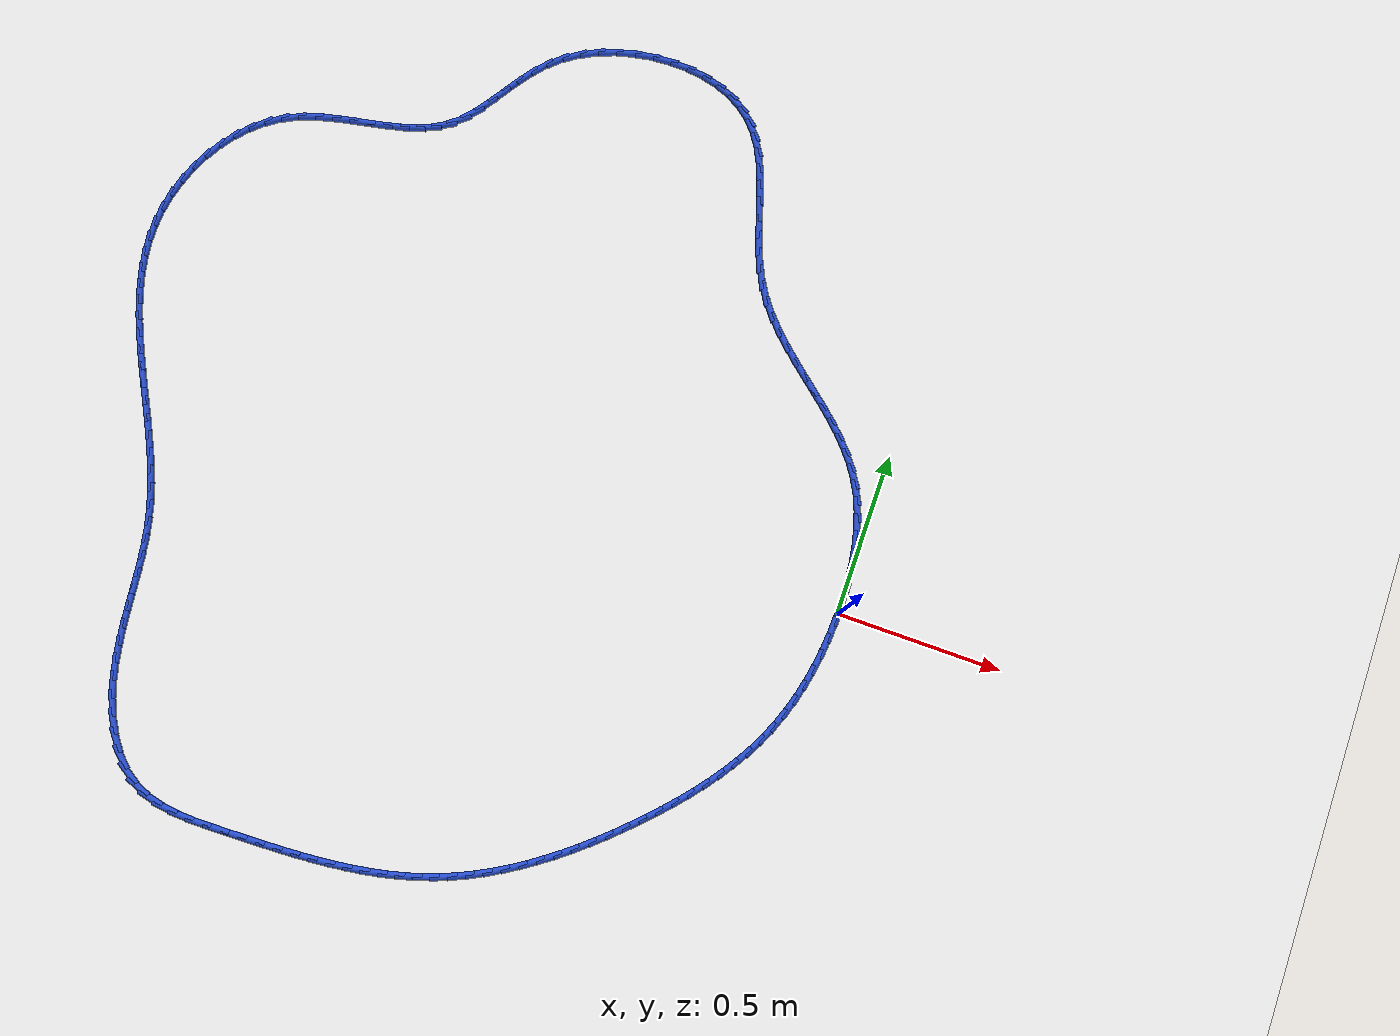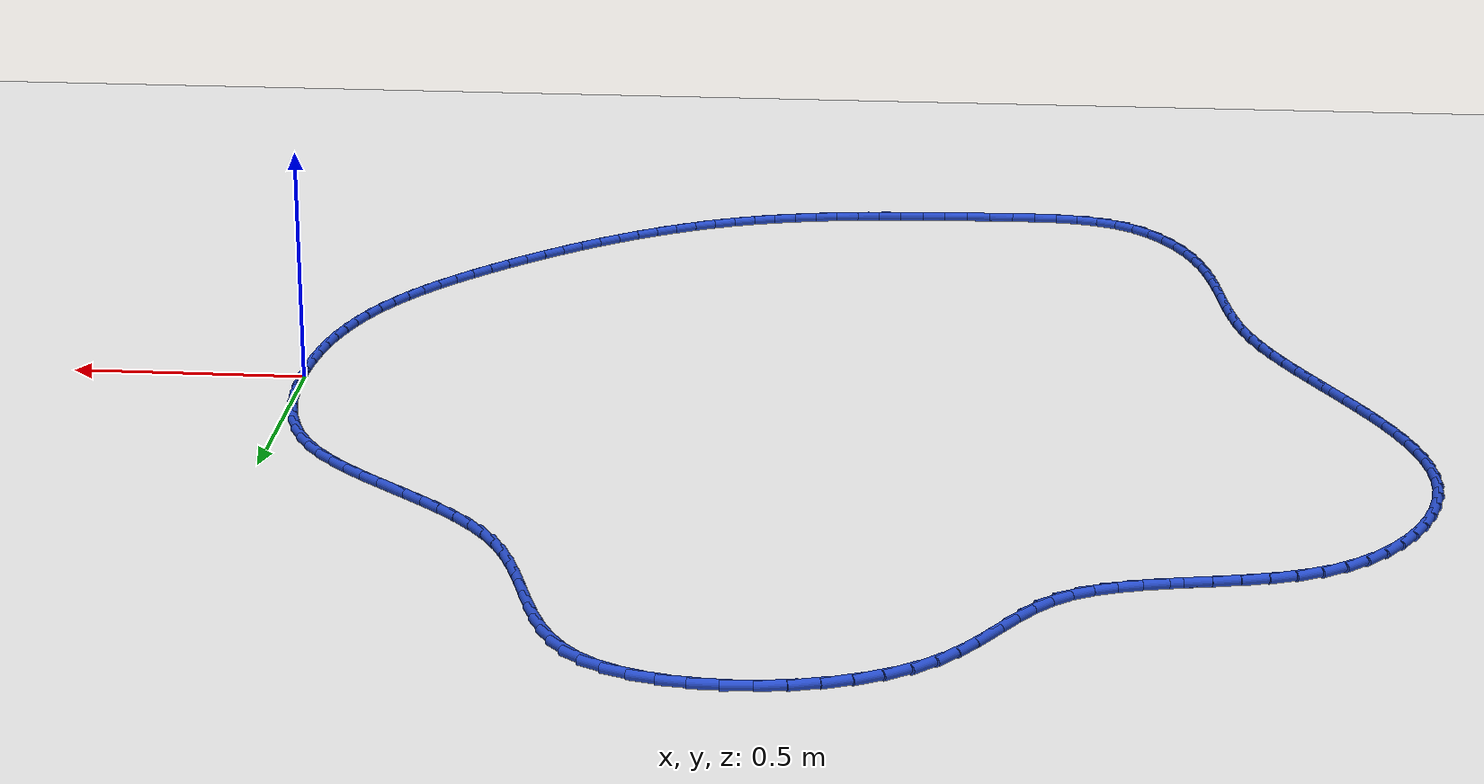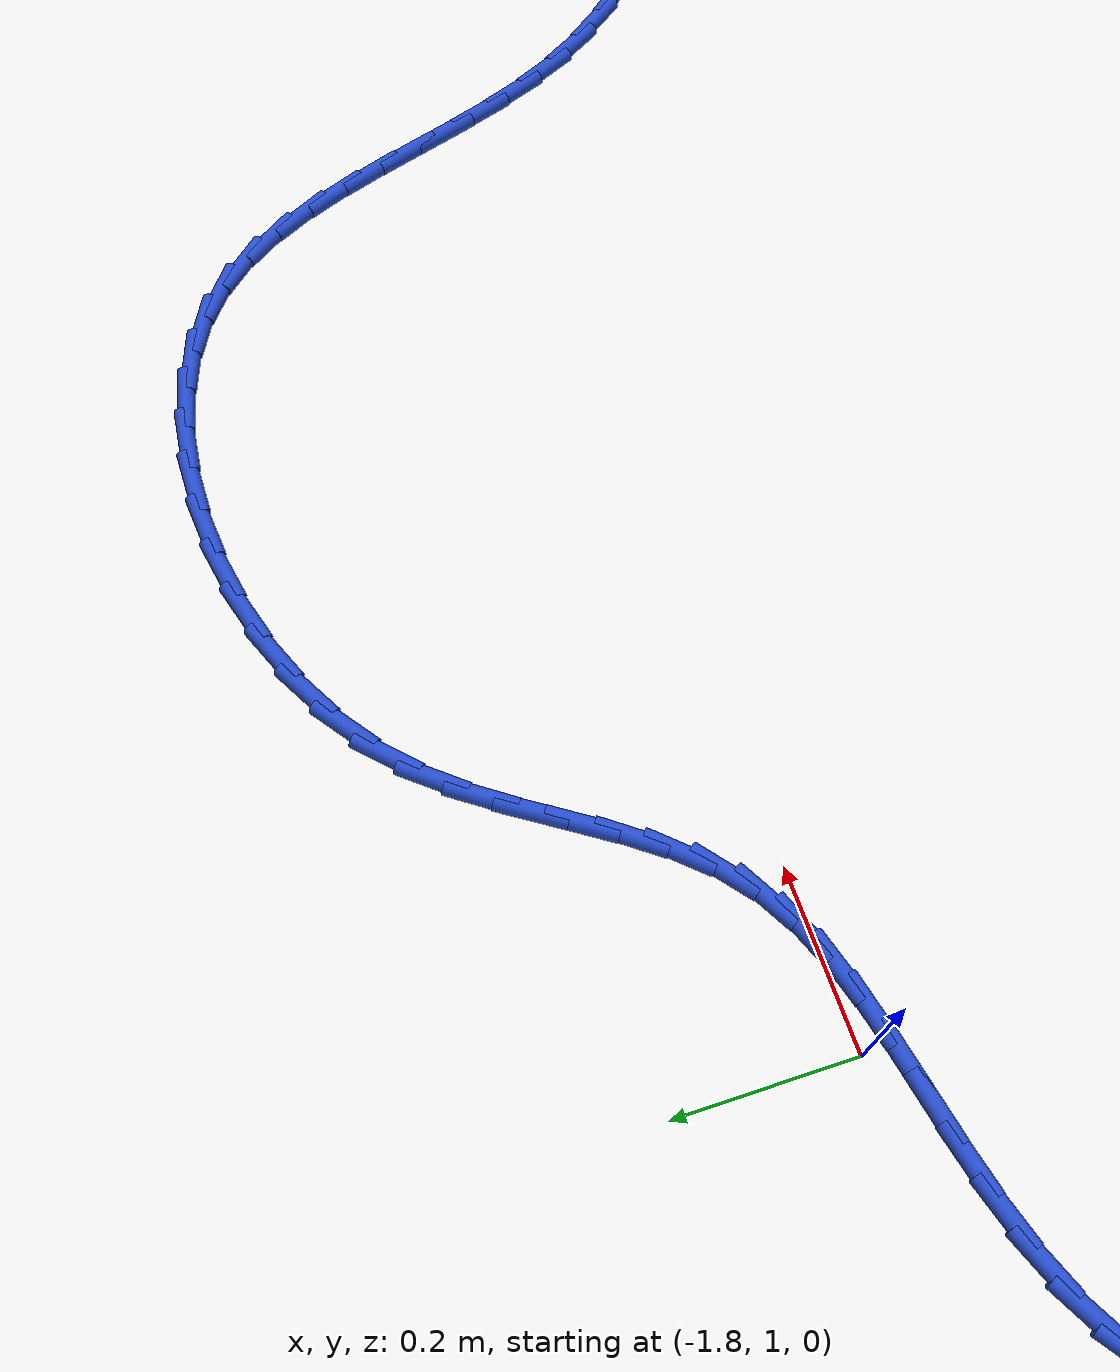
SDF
<sdf version="1.6">
 <world name="default">
  <light name="sun" type="directional">
   <pose>0 0 10 0 -0 0</pose>
   <diffuse>0.8 0.8 0.8 1</diffuse>
   <specular>0.2 0.2 0.2 1</specular>
   <attenuation>
    <range>1000</range>
    <constant>0.9</constant>
    <linear>0.01</linear>
    <quadratic>0.001</quadratic>
   </attenuation>
   <direction>-0.5 0.1 -0.9</direction>
  </light>
  <model name="ground_plane">
   <static>1</static>
   <link name="link">
    <collision name="collision">
     <geometry><plane><normal>0 0 1</normal><size>100 100</size></plane></geometry>
     <surface><friction><ode><mu>100</mu><mu2>50</mu2></ode></friction></surface>
    </collision>
    <visual name="visual">
     <cast_shadows>0</cast_shadows>
     <geometry><plane><normal>0 0 1</normal><size>100 100</size></plane></geometry>
     <material>
      <script><uri>file://media/materials/scripts/gazebo.material</uri><name>Gazebo/WhiteGlow</name></script>
     </material>
    </visual>
   </link>
  </model>
  <gravity>0 0 -9.8</gravity>
  <magnetic_field>6e-06 2.3e-05 -4.2e-05</magnetic_field>
  <atmosphere type="adiabatic"/>
  <physics name="default_physics" default="0" type="ode">
   <max_step_size>0.001</max_step_size>
   <real_time_factor>1</real_time_factor>
   <real_time_update_rate>1000</real_time_update_rate>
  </physics>
  <scene><ambient>0.4 0.4 0.4 1</ambient><background>0.7 0.7 0.7 1</background><shadows>1</shadows></scene>
  <spherical_coordinates>
   <surface_model>EARTH_WGS84</surface_model>
   <latitude_deg>0</latitude_deg>
   <longitude_deg>0</longitude_deg>
   <elevation>0</elevation>
   <heading_deg>0</heading_deg>
  </spherical_coordinates>
  <model name="line">
   <link name="link_0">
    <pose>6.071532165918825e-18 4.163336342344337e-17 0.01 0 1.57 -1.570722538413021</pose>
    <collision name="collision">
     <geometry><cylinder><radius>0.01</radius><length>0.08</length></cylinder></geometry>
    </collision>
    <visual name="visual">
     <material>
      <script><name>Gazebo/Blue</name><uri>file://media/materials/scripts/gazebo.material</uri></script>
     </material>
     <geometry><cylinder><radius>0.01</radius><length>0.08</length></cylinder></geometry>
    </visual>
   </link>
   <link name="link_1">
    <pose>-3.95585154420227e-06 0.053610764140245896 0.01 0 1.57 -1.5251461251662592</pose>
    <collision name="collision">
     <geometry><cylinder><radius>0.01</radius><length>0.08</length></cylinder></geometry>
    </collision>
    <visual name="visual">
     <material>
      <script><name>Gazebo/Blue</name><uri>file://media/materials/scripts/gazebo.material</uri></script>
     </material>
     <geometry><cylinder><radius>0.01</radius><length>0.08</length></cylinder></geometry>
    </visual>
   </link>
   <link name="link_2">
    <pose>-0.002452437122463699 0.10720921753562955 0.01 0 1.57 -1.4734195790212294</pose>
    <collision name="collision">
     <geometry><cylinder><radius>0.01</radius><length>0.08</length></cylinder></geometry>
    </collision>
    <visual name="visual">
     <material>
      <script><name>Gazebo/Blue</name><uri>file://media/materials/scripts/gazebo.material</uri></script>
     </material>
     <geometry><cylinder><radius>0.01</radius><length>0.08</length></cylinder></geometry>
    </visual>
   </link>
   <link name="link_3">
    <pose>-0.007645587806940951 0.16037104722370726 0.01 0 1.57 -1.4145689094842695</pose>
    <collision name="collision">
     <geometry><cylinder><radius>0.01</radius><length>0.08</length></cylinder></geometry>
    </collision>
    <visual name="visual">
     <material>
      <script><name>Gazebo/Blue</name><uri>file://media/materials/scripts/gazebo.material</uri></script>
     </material>
     <geometry><cylinder><radius>0.01</radius><length>0.08</length></cylinder></geometry>
    </visual>
   </link>
   <link name="link_4">
    <pose>-0.01588355189915844 0.21267194024203526 0.01 0 1.57 -1.3475348852987874</pose>
    <collision name="collision">
     <geometry><cylinder><radius>0.01</radius><length>0.08</length></cylinder></geometry>
    </collision>
    <visual name="visual">
     <material>
      <script><name>Gazebo/Blue</name><uri>file://media/materials/scripts/gazebo.material</uri></script>
     </material>
     <geometry><cylinder><radius>0.01</radius><length>0.08</length></cylinder></geometry>
    </visual>
   </link>
   <link name="link_5">
    <pose>-0.027466473393298618 0.2636875836281699 0.01 0 1.57 -1.2712431375198436</pose>
    <collision name="collision">
     <geometry><cylinder><radius>0.01</radius><length>0.08</length></cylinder></geometry>
    </collision>
    <visual name="visual">
     <material>
      <script><name>Gazebo/Blue</name><uri>file://media/materials/scripts/gazebo.material</uri></script>
     </material>
     <geometry><cylinder><radius>0.01</radius><length>0.08</length></cylinder></geometry>
    </visual>
   </link>
   <link name="link_6">
    <pose>-0.04269449628354397 0.31299366441966764 0.01 0 1.57 -1.184739718715511</pose>
    <collision name="collision">
     <geometry><cylinder><radius>0.01</radius><length>0.08</length></cylinder></geometry>
    </collision>
    <visual name="visual">
     <material>
      <script><name>Gazebo/Blue</name><uri>file://media/materials/scripts/gazebo.material</uri></script>
     </material>
     <geometry><cylinder><radius>0.01</radius><length>0.08</length></cylinder></geometry>
    </visual>
   </link>
   <link name="link_7">
    <pose>-0.061867764564076985 0.3601658696540845 0.01 0 1.57 -1.087414361031131</pose>
    <collision name="collision">
     <geometry><cylinder><radius>0.01</radius><length>0.08</length></cylinder></geometry>
    </collision>
    <visual name="visual">
     <material>
      <script><name>Gazebo/Blue</name><uri>file://media/materials/scripts/gazebo.material</uri></script>
     </material>
     <geometry><cylinder><radius>0.01</radius><length>0.08</length></cylinder></geometry>
    </visual>
   </link>
   <link name="link_8">
    <pose>-0.0852864222290801 0.4047798863689768 0.01 0 1.57 -0.9832801934481397</pose>
    <collision name="collision">
     <geometry><cylinder><radius>0.01</radius><length>0.08</length></cylinder></geometry>
    </collision>
    <visual name="visual">
     <material>
      <script><name>Gazebo/Blue</name><uri>file://media/materials/scripts/gazebo.material</uri></script>
     </material>
     <geometry><cylinder><radius>0.01</radius><length>0.08</length></cylinder></geometry>
    </visual>
   </link>
   <link name="link_9">
    <pose>-0.11310188970390438 0.4465470967355545 0.01 0 1.57 -0.8917381367777042</pose>
    <collision name="collision">
     <geometry><cylinder><radius>0.01</radius><length>0.08</length></cylinder></geometry>
    </collision>
    <visual name="visual">
     <material>
      <script><name>Gazebo/Blue</name><uri>file://media/materials/scripts/gazebo.material</uri></script>
     </material>
     <geometry><cylinder><radius>0.01</radius><length>0.08</length></cylinder></geometry>
    </visual>
   </link>
   <link name="link_10">
    <pose>-0.14478383539780804 0.48580091231599154 0.01 0 1.57 -0.8190879116231532</pose>
    <collision name="collision">
     <geometry><cylinder><radius>0.01</radius><length>0.08</length></cylinder></geometry>
    </collision>
    <visual name="visual">
     <material>
      <script><name>Gazebo/Blue</name><uri>file://media/materials/scripts/gazebo.material</uri></script>
     </material>
     <geometry><cylinder><radius>0.01</radius><length>0.08</length></cylinder></geometry>
    </visual>
   </link>
   <link name="link_11">
    <pose>-0.1796066955611529 0.5230528741653403 0.01 0 1.57 -0.7651744274622446</pose>
    <collision name="collision">
     <geometry><cylinder><radius>0.01</radius><length>0.08</length></cylinder></geometry>
    </collision>
    <visual name="visual">
     <material>
      <script><name>Gazebo/Blue</name><uri>file://media/materials/scripts/gazebo.material</uri></script>
     </material>
     <geometry><cylinder><radius>0.01</radius><length>0.08</length></cylinder></geometry>
    </visual>
   </link>
   <link name="link_12">
    <pose>-0.2168448904751476 0.558814537908881 0.01 0 1.57 -0.7292237114786965</pose>
    <collision name="collision">
     <geometry><cylinder><radius>0.01</radius><length>0.08</length></cylinder></geometry>
    </collision>
    <visual name="visual">
     <material>
      <script><name>Gazebo/Blue</name><uri>file://media/materials/scripts/gazebo.material</uri></script>
     </material>
     <geometry><cylinder><radius>0.01</radius><length>0.08</length></cylinder></geometry>
    </visual>
   </link>
   <link name="link_13">
    <pose>-0.2557728404210007 0.5935974591718944 0.01 0 1.57 -0.7103935757408499</pose>
    <collision name="collision">
     <geometry><cylinder><radius>0.01</radius><length>0.08</length></cylinder></geometry>
    </collision>
    <visual name="visual">
     <material>
      <script><name>Gazebo/Blue</name><uri>file://media/materials/scripts/gazebo.material</uri></script>
     </material>
     <geometry><cylinder><radius>0.01</radius><length>0.08</length></cylinder></geometry>
    </visual>
   </link>
   <link name="link_14">
    <pose>-0.29566496567992073 0.6279131935796609 0.01 0 1.57 -0.7080850772625676</pose>
    <collision name="collision">
     <geometry><cylinder><radius>0.01</radius><length>0.08</length></cylinder></geometry>
    </collision>
    <visual name="visual">
     <material>
      <script><name>Gazebo/Blue</name><uri>file://media/materials/scripts/gazebo.material</uri></script>
     </material>
     <geometry><cylinder><radius>0.01</radius><length>0.08</length></cylinder></geometry>
    </visual>
   </link>
   <link name="link_15">
    <pose>-0.33579568653311626 0.6622732967574612 0.01 0 1.57 -0.7220746223140687</pose>
    <collision name="collision">
     <geometry><cylinder><radius>0.01</radius><length>0.08</length></cylinder></geometry>
    </collision>
    <visual name="visual">
     <material>
      <script><name>Gazebo/Blue</name><uri>file://media/materials/scripts/gazebo.material</uri></script>
     </material>
     <geometry><cylinder><radius>0.01</radius><length>0.08</length></cylinder></geometry>
    </visual>
   </link>
   <link name="link_16">
    <pose>-0.3754394232617959 0.6971893243305755 0.01 0 1.57 -0.752517780932649</pose>
    <collision name="collision">
     <geometry><cylinder><radius>0.01</radius><length>0.08</length></cylinder></geometry>
    </collision>
    <visual name="visual">
     <material>
      <script><name>Gazebo/Blue</name><uri>file://media/materials/scripts/gazebo.material</uri></script>
     </material>
     <geometry><cylinder><radius>0.01</radius><length>0.08</length></cylinder></geometry>
    </visual>
   </link>
   <link name="link_17">
    <pose>-0.41387059614716837 0.7331728319242845 0.01 0 1.57 -0.7998392045167213</pose>
    <collision name="collision">
     <geometry><cylinder><radius>0.01</radius><length>0.08</length></cylinder></geometry>
    </collision>
    <visual name="visual">
     <material>
      <script><name>Gazebo/Blue</name><uri>file://media/materials/scripts/gazebo.material</uri></script>
     </material>
     <geometry><cylinder><radius>0.01</radius><length>0.08</length></cylinder></geometry>
    </visual>
   </link>
   <link name="link_18">
    <pose>-0.450363625470442 0.7707353751638686 0.01 0 1.57 -0.8644875407225124</pose>
    <collision name="collision">
     <geometry><cylinder><radius>0.01</radius><length>0.08</length></cylinder></geometry>
    </collision>
    <visual name="visual">
     <material>
      <script><name>Gazebo/Blue</name><uri>file://media/materials/scripts/gazebo.material</uri></script>
     </material>
     <geometry><cylinder><radius>0.01</radius><length>0.08</length></cylinder></geometry>
    </visual>
   </link>
   <link name="link_19">
    <pose>-0.4841929315128255 0.8103885096746084 0.01 0 1.57 -0.9465208209089788</pose>
    <collision name="collision">
     <geometry><cylinder><radius>0.01</radius><length>0.08</length></cylinder></geometry>
    </collision>
    <visual name="visual">
     <material>
      <script><name>Gazebo/Blue</name><uri>file://media/materials/scripts/gazebo.material</uri></script>
     </material>
     <geometry><cylinder><radius>0.01</radius><length>0.08</length></cylinder></geometry>
    </visual>
   </link>
   <link name="link_20">
    <pose>-0.5146329345555274 0.8526437910817841 0.01 0 1.57 -1.044610553574459</pose>
    <collision name="collision">
     <geometry><cylinder><radius>0.01</radius><length>0.08</length></cylinder></geometry>
    </collision>
    <visual name="visual">
     <material>
      <script><name>Gazebo/Blue</name><uri>file://media/materials/scripts/gazebo.material</uri></script>
     </material>
     <geometry><cylinder><radius>0.01</radius><length>0.08</length></cylinder></geometry>
    </visual>
   </link>
   <link name="link_21">
    <pose>-0.5409754587103622 0.8979990045110348 0.01 0 1.57 -1.139596820807599</pose>
    <collision name="collision">
     <geometry><cylinder><radius>0.01</radius><length>0.08</length></cylinder></geometry>
    </collision>
    <visual name="visual">
     <material>
      <script><name>Gazebo/Blue</name><uri>file://media/materials/scripts/gazebo.material</uri></script>
     </material>
     <geometry><cylinder><radius>0.01</radius><length>0.08</length></cylinder></geometry>
    </visual>
   </link>
   <link name="link_22">
    <pose>-0.5632345159282068 0.9463805156341539 0.01 0 1.57 -1.208715671980354</pose>
    <collision name="collision">
     <geometry><cylinder><radius>0.01</radius><length>0.08</length></cylinder></geometry>
    </collision>
    <visual name="visual">
     <material>
      <script><name>Gazebo/Blue</name><uri>file://media/materials/scripts/gazebo.material</uri></script>
     </material>
     <geometry><cylinder><radius>0.01</radius><length>0.08</length></cylinder></geometry>
    </visual>
   </link>
   <link name="link_23">
    <pose>-0.5823895416364918 0.9969508144027122 0.01 0 1.57 -1.2523751088850654</pose>
    <collision name="collision">
     <geometry><cylinder><radius>0.01</radius><length>0.08</length></cylinder></geometry>
    </collision>
    <visual name="visual">
     <material>
      <script><name>Gazebo/Blue</name><uri>file://media/materials/scripts/gazebo.material</uri></script>
     </material>
     <geometry><cylinder><radius>0.01</radius><length>0.08</length></cylinder></geometry>
    </visual>
   </link>
   <link name="link_24">
    <pose>-0.5994873108480153 1.0488191094098702 0.01 0 1.57 -1.2722533842479706</pose>
    <collision name="collision">
     <geometry><cylinder><radius>0.01</radius><length>0.08</length></cylinder></geometry>
    </collision>
    <visual name="visual">
     <material>
      <script><name>Gazebo/Blue</name><uri>file://media/materials/scripts/gazebo.material</uri></script>
     </material>
     <geometry><cylinder><radius>0.01</radius><length>0.08</length></cylinder></geometry>
    </visual>
   </link>
   <link name="link_25">
    <pose>-0.6155745985755753 1.101094609248789 0.01 0 1.57 -1.2689917160222215</pose>
    <collision name="collision">
     <geometry><cylinder><radius>0.01</radius><length>0.08</length></cylinder></geometry>
    </collision>
    <visual name="visual">
     <material>
      <script><name>Gazebo/Blue</name><uri>file://media/materials/scripts/gazebo.material</uri></script>
     </material>
     <geometry><cylinder><radius>0.01</radius><length>0.08</length></cylinder></geometry>
    </visual>
   </link>
   <link name="link_26">
    <pose>-0.6316981798319699 1.152886522512628 0.01 0 1.57 -1.2419081788691613</pose>
    <collision name="collision">
     <geometry><cylinder><radius>0.01</radius><length>0.08</length></cylinder></geometry>
    </collision>
    <visual name="visual">
     <material>
      <script><name>Gazebo/Blue</name><uri>file://media/materials/scripts/gazebo.material</uri></script>
     </material>
     <geometry><cylinder><radius>0.01</radius><length>0.08</length></cylinder></geometry>
    </visual>
   </link>
   <link name="link_27">
    <pose>-0.6489048296299971 1.2033040577945489 0.01 0 1.57 -1.188938168429718</pose>
    <collision name="collision">
     <geometry><cylinder><radius>0.01</radius><length>0.08</length></cylinder></geometry>
    </collision>
    <visual name="visual">
     <material>
      <script><name>Gazebo/Blue</name><uri>file://media/materials/scripts/gazebo.material</uri></script>
     </material>
     <geometry><cylinder><radius>0.01</radius><length>0.08</length></cylinder></geometry>
    </visual>
   </link>
   <link name="link_28">
    <pose>-0.6682413229824546 1.2514564236877113 0.01 0 1.57 -1.106883676269616</pose>
    <collision name="collision">
     <geometry><cylinder><radius>0.01</radius><length>0.08</length></cylinder></geometry>
    </collision>
    <visual name="visual">
     <material>
      <script><name>Gazebo/Blue</name><uri>file://media/materials/scripts/gazebo.material</uri></script>
     </material>
     <geometry><cylinder><radius>0.01</radius><length>0.08</length></cylinder></geometry>
    </visual>
   </link>
   <link name="link_29">
    <pose>-0.690754434902141 1.296452828785276 0.01 0 1.57 -0.9923769735052378</pose>
    <collision name="collision">
     <geometry><cylinder><radius>0.01</radius><length>0.08</length></cylinder></geometry>
    </collision>
    <visual name="visual">
     <material>
      <script><name>Gazebo/Blue</name><uri>file://media/materials/scripts/gazebo.material</uri></script>
     </material>
     <geometry><cylinder><radius>0.01</radius><length>0.08</length></cylinder></geometry>
    </visual>
   </link>
   <link name="link_30">
    <pose>-0.717490940401854 1.3374024816804035 0.01 0 1.57 -0.8442174294790669</pose>
    <collision name="collision">
     <geometry><cylinder><radius>0.01</radius><length>0.08</length></cylinder></geometry>
    </collision>
    <visual name="visual">
     <material>
      <script><name>Gazebo/Blue</name><uri>file://media/materials/scripts/gazebo.material</uri></script>
     </material>
     <geometry><cylinder><radius>0.01</radius><length>0.08</length></cylinder></geometry>
    </visual>
   </link>
   <link name="link_31">
    <pose>-0.7494976144943917 1.3734145909662545 0.01 0 1.57 -0.6690987243588585</pose>
    <collision name="collision">
     <geometry><cylinder><radius>0.01</radius><length>0.08</length></cylinder></geometry>
    </collision>
    <visual name="visual">
     <material>
      <script><name>Gazebo/Blue</name><uri>file://media/materials/scripts/gazebo.material</uri></script>
     </material>
     <geometry><cylinder><radius>0.01</radius><length>0.08</length></cylinder></geometry>
    </visual>
   </link>
   <link name="link_32">
    <pose>-0.7877231225606998 1.403642873394109 0.01 0 1.57 -0.5000693617341696</pose>
    <collision name="collision">
     <geometry><cylinder><radius>0.01</radius><length>0.08</length></cylinder></geometry>
    </collision>
    <visual name="visual">
     <material>
      <script><name>Gazebo/Blue</name><uri>file://media/materials/scripts/gazebo.material</uri></script>
     </material>
     <geometry><cylinder><radius>0.01</radius><length>0.08</length></cylinder></geometry>
    </visual>
   </link>
   <link name="link_33">
    <pose>-0.83191196109078 1.4277873258142504 0.01 0 1.57 -0.3537444397103643</pose>
    <collision name="collision">
     <geometry><cylinder><radius>0.01</radius><length>0.08</length></cylinder></geometry>
    </collision>
    <visual name="visual">
     <material>
      <script><name>Gazebo/Blue</name><uri>file://media/materials/scripts/gazebo.material</uri></script>
     </material>
     <geometry><cylinder><radius>0.01</radius><length>0.08</length></cylinder></geometry>
    </visual>
   </link>
   <link name="link_34">
    <pose>-0.8810004142499142 1.4459145965592266 0.01 0 1.57 -0.2263260969041418</pose>
    <collision name="collision">
     <geometry><cylinder><radius>0.01</radius><length>0.08</length></cylinder></geometry>
    </collision>
    <visual name="visual">
     <material>
      <script><name>Gazebo/Blue</name><uri>file://media/materials/scripts/gazebo.material</uri></script>
     </material>
     <geometry><cylinder><radius>0.01</radius><length>0.08</length></cylinder></geometry>
    </visual>
   </link>
   <link name="link_35">
    <pose>-0.9339098158405071 1.4580981163039743 0.01 0 1.57 -0.11295840158054156</pose>
    <collision name="collision">
     <geometry><cylinder><radius>0.01</radius><length>0.08</length></cylinder></geometry>
    </collision>
    <visual name="visual">
     <material>
      <script><name>Gazebo/Blue</name><uri>file://media/materials/scripts/gazebo.material</uri></script>
     </material>
     <geometry><cylinder><radius>0.01</radius><length>0.08</length></cylinder></geometry>
    </visual>
   </link>
   <link name="link_36">
    <pose>-0.9895614996649659 1.4644113157234309 0.01 0 1.57 -0.00900799272002091</pose>
    <collision name="collision">
     <geometry><cylinder><radius>0.01</radius><length>0.08</length></cylinder></geometry>
    </collision>
    <visual name="visual">
     <material>
      <script><name>Gazebo/Blue</name><uri>file://media/materials/scripts/gazebo.material</uri></script>
     </material>
     <geometry><cylinder><radius>0.01</radius><length>0.08</length></cylinder></geometry>
    </visual>
   </link>
   <link name="link_37">
    <pose>-1.046876799525695 1.4649276254925327 0.01 0 1.57 0.08969181578536496</pose>
    <collision name="collision">
     <geometry><cylinder><radius>0.01</radius><length>0.08</length></cylinder></geometry>
    </collision>
    <visual name="visual">
     <material>
      <script><name>Gazebo/Blue</name><uri>file://media/materials/scripts/gazebo.material</uri></script>
     </material>
     <geometry><cylinder><radius>0.01</radius><length>0.08</length></cylinder></geometry>
    </visual>
   </link>
   <link name="link_38">
    <pose>-1.1047770492251012 1.4597204762862173 0.01 0 1.57 0.1869201048515047</pose>
    <collision name="collision">
     <geometry><cylinder><radius>0.01</radius><length>0.08</length></cylinder></geometry>
    </collision>
    <visual name="visual">
     <material>
      <script><name>Gazebo/Blue</name><uri>file://media/materials/scripts/gazebo.material</uri></script>
     </material>
     <geometry><cylinder><radius>0.01</radius><length>0.08</length></cylinder></geometry>
    </visual>
   </link>
   <link name="link_39">
    <pose>-1.16218358256559 1.4488632987794212 0.01 0 1.57 0.28624868168233814</pose>
    <collision name="collision">
     <geometry><cylinder><radius>0.01</radius><length>0.08</length></cylinder></geometry>
    </collision>
    <visual name="visual">
     <material>
      <script><name>Gazebo/Blue</name><uri>file://media/materials/scripts/gazebo.material</uri></script>
     </material>
     <geometry><cylinder><radius>0.01</radius><length>0.08</length></cylinder></geometry>
    </visual>
   </link>
   <link name="link_40">
    <pose>-1.2180177333495668 1.4324295236470805 0.01 0 1.57 0.3912181041498231</pose>
    <collision name="collision">
     <geometry><cylinder><radius>0.01</radius><length>0.08</length></cylinder></geometry>
    </collision>
    <visual name="visual">
     <material>
      <script><name>Gazebo/Blue</name><uri>file://media/materials/scripts/gazebo.material</uri></script>
     </material>
     <geometry><cylinder><radius>0.01</radius><length>0.08</length></cylinder></geometry>
    </visual>
   </link>
   <link name="link_41">
    <pose>-1.2712008353794386 1.410492581564133 0.01 0 1.57 0.5054370398451392</pose>
    <collision name="collision">
     <geometry><cylinder><radius>0.01</radius><length>0.08</length></cylinder></geometry>
    </collision>
    <visual name="visual">
     <material>
      <script><name>Gazebo/Blue</name><uri>file://media/materials/scripts/gazebo.material</uri></script>
     </material>
     <geometry><cylinder><radius>0.01</radius><length>0.08</length></cylinder></geometry>
    </visual>
   </link>
   <link name="link_42">
    <pose>-1.3206542224576097 1.383125903205515 0.01 0 1.57 0.6325057318195535</pose>
    <collision name="collision">
     <geometry><cylinder><radius>0.01</radius><length>0.08</length></cylinder></geometry>
    </collision>
    <visual name="visual">
     <material>
      <script><name>Gazebo/Blue</name><uri>file://media/materials/scripts/gazebo.material</uri></script>
     </material>
     <geometry><cylinder><radius>0.01</radius><length>0.08</length></cylinder></geometry>
    </visual>
   </link>
   <link name="link_43">
    <pose>-1.3652992283864869 1.3504029192461637 0.01 0 1.57 0.771501947671214</pose>
    <collision name="collision">
     <geometry><cylinder><radius>0.01</radius><length>0.08</length></cylinder></geometry>
    </collision>
    <visual name="visual">
     <material>
      <script><name>Gazebo/Blue</name><uri>file://media/materials/scripts/gazebo.material</uri></script>
     </material>
     <geometry><cylinder><radius>0.01</radius><length>0.08</length></cylinder></geometry>
    </visual>
   </link>
   <link name="link_44">
    <pose>-1.4042523132137743 1.3125176652860229 0.01 0 1.57 0.8883792527109948</pose>
    <collision name="collision">
     <geometry><cylinder><radius>0.01</radius><length>0.08</length></cylinder></geometry>
    </collision>
    <visual name="visual">
     <material>
      <script><name>Gazebo/Blue</name><uri>file://media/materials/scripts/gazebo.material</uri></script>
     </material>
     <geometry><cylinder><radius>0.01</radius><length>0.08</length></cylinder></geometry>
    </visual>
   </link>
   <link name="link_45">
    <pose>-1.4382594316013602 1.2706713457732917 0.01 0 1.57 0.9639726438780598</pose>
    <collision name="collision">
     <geometry><cylinder><radius>0.01</radius><length>0.08</length></cylinder></geometry>
    </collision>
    <visual name="visual">
     <material>
      <script><name>Gazebo/Blue</name><uri>file://media/materials/scripts/gazebo.material</uri></script>
     </material>
     <geometry><cylinder><radius>0.01</radius><length>0.08</length></cylinder></geometry>
    </visual>
   </link>
   <link name="link_46">
    <pose>-1.4688772483453576 1.226566254257696 0.01 0 1.57 0.9981541267013552</pose>
    <collision name="collision">
     <geometry><cylinder><radius>0.01</radius><length>0.08</length></cylinder></geometry>
    </collision>
    <visual name="visual">
     <material>
      <script><name>Gazebo/Blue</name><uri>file://media/materials/scripts/gazebo.material</uri></script>
     </material>
     <geometry><cylinder><radius>0.01</radius><length>0.08</length></cylinder></geometry>
    </visual>
   </link>
   <link name="link_47">
    <pose>-1.4976683280133842 1.181908330858896 0.01 0 1.57 0.9904116496803475</pose>
    <collision name="collision">
     <geometry><cylinder><radius>0.01</radius><length>0.08</length></cylinder></geometry>
    </collision>
    <visual name="visual">
     <material>
      <script><name>Gazebo/Blue</name><uri>file://media/materials/scripts/gazebo.material</uri></script>
     </material>
     <geometry><cylinder><radius>0.01</radius><length>0.08</length></cylinder></geometry>
    </visual>
   </link>
   <link name="link_48">
    <pose>-1.526195235173056 1.13840351569655 0.01 0 1.57 0.9377531179695614</pose>
    <collision name="collision">
     <geometry><cylinder><radius>0.01</radius><length>0.08</length></cylinder></geometry>
    </collision>
    <visual name="visual">
     <material>
      <script><name>Gazebo/Blue</name><uri>file://media/materials/scripts/gazebo.material</uri></script>
     </material>
     <geometry><cylinder><radius>0.01</radius><length>0.08</length></cylinder></geometry>
    </visual>
   </link>
   <link name="link_49">
    <pose>-1.55602053439199 1.0977577488903179 0.01 0 1.57 0.8347207703461984</pose>
    <collision name="collision">
     <geometry><cylinder><radius>0.01</radius><length>0.08</length></cylinder></geometry>
    </collision>
    <visual name="visual">
     <material>
      <script><name>Gazebo/Blue</name><uri>file://media/materials/scripts/gazebo.material</uri></script>
     </material>
     <geometry><cylinder><radius>0.01</radius><length>0.08</length></cylinder></geometry>
    </visual>
   </link>
   <link name="link_50">
    <pose>-1.5887067902378011 1.061676970559858 0.01 0 1.57 0.6777907222157921</pose>
    <collision name="collision">
     <geometry><cylinder><radius>0.01</radius><length>0.08</length></cylinder></geometry>
    </collision>
    <visual name="visual">
     <material>
      <script><name>Gazebo/Blue</name><uri>file://media/materials/scripts/gazebo.material</uri></script>
     </material>
     <geometry><cylinder><radius>0.01</radius><length>0.08</length></cylinder></geometry>
    </visual>
   </link>
   <link name="link_51">
    <pose>-1.6257854610123526 1.031828125647558 0.01 0 1.57 0.5065853276404212</pose>
    <collision name="collision">
     <geometry><cylinder><radius>0.01</radius><length>0.08</length></cylinder></geometry>
    </collision>
    <visual name="visual">
     <material>
      <script><name>Gazebo/Blue</name><uri>file://media/materials/scripts/gazebo.material</uri></script>
     </material>
     <geometry><cylinder><radius>0.01</radius><length>0.08</length></cylinder></geometry>
    </visual>
   </link>
   <link name="link_52">
    <pose>-1.6677310687088054 1.0085531714212772 0.01 0 1.57 0.3725883030408081</pose>
    <collision name="collision">
     <geometry><cylinder><radius>0.01</radius><length>0.08</length></cylinder></geometry>
    </collision>
    <visual name="visual">
     <material>
      <script><name>Gazebo/Blue</name><uri>file://media/materials/scripts/gazebo.material</uri></script>
     </material>
     <geometry><cylinder><radius>0.01</radius><length>0.08</length></cylinder></geometry>
    </visual>
   </link>
   <link name="link_53">
    <pose>-1.713727280966982 0.9905758350874241 0.01 0 1.57 0.27850542384754723</pose>
    <collision name="collision">
     <geometry><cylinder><radius>0.01</radius><length>0.08</length></cylinder></geometry>
    </collision>
    <visual name="visual">
     <material>
      <script><name>Gazebo/Blue</name><uri>file://media/materials/scripts/gazebo.material</uri></script>
     </material>
     <geometry><cylinder><radius>0.01</radius><length>0.08</length></cylinder></geometry>
    </visual>
   </link>
   <link name="link_54">
    <pose>-1.7628792885585582 0.976521464335898 0.01 0 1.57 0.22016881367419885</pose>
    <collision name="collision">
     <geometry><cylinder><radius>0.01</radius><length>0.08</length></cylinder></geometry>
    </collision>
    <visual name="visual">
     <material>
      <script><name>Gazebo/Blue</name><uri>file://media/materials/scripts/gazebo.material</uri></script>
     </material>
     <geometry><cylinder><radius>0.01</radius><length>0.08</length></cylinder></geometry>
    </visual>
   </link>
   <link name="link_55">
    <pose>-1.8142922822552097 0.9650154068565991 0.01 0 1.57 0.19332164766365995</pose>
    <collision name="collision">
     <geometry><cylinder><radius>0.01</radius><length>0.08</length></cylinder></geometry>
    </collision>
    <visual name="visual">
     <material>
      <script><name>Gazebo/Blue</name><uri>file://media/materials/scripts/gazebo.material</uri></script>
     </material>
     <geometry><cylinder><radius>0.01</radius><length>0.08</length></cylinder></geometry>
    </visual>
   </link>
   <link name="link_56">
    <pose>-1.8670714528286125 0.9546830103394278 0.01 0 1.57 0.19528707941820816</pose>
    <collision name="collision">
     <geometry><cylinder><radius>0.01</radius><length>0.08</length></cylinder></geometry>
    </collision>
    <visual name="visual">
     <material>
      <script><name>Gazebo/Blue</name><uri>file://media/materials/scripts/gazebo.material</uri></script>
     </material>
     <geometry><cylinder><radius>0.01</radius><length>0.08</length></cylinder></geometry>
    </visual>
   </link>
   <link name="link_57">
    <pose>-1.9203219910504428 0.9441496224742838 0.01 0 1.57 0.22532753048001988</pose>
    <collision name="collision">
     <geometry><cylinder><radius>0.01</radius><length>0.08</length></cylinder></geometry>
    </collision>
    <visual name="visual">
     <material>
      <script><name>Gazebo/Blue</name><uri>file://media/materials/scripts/gazebo.material</uri></script>
     </material>
     <geometry><cylinder><radius>0.01</radius><length>0.08</length></cylinder></geometry>
    </visual>
   </link>
   <link name="link_58">
    <pose>-1.973149087692377 0.9320405909510673 0.01 0 1.57 0.284436566805066</pose>
    <collision name="collision">
     <geometry><cylinder><radius>0.01</radius><length>0.08</length></cylinder></geometry>
    </collision>
    <visual name="visual">
     <material>
      <script><name>Gazebo/Blue</name><uri>file://media/materials/scripts/gazebo.material</uri></script>
     </material>
     <geometry><cylinder><radius>0.01</radius><length>0.08</length></cylinder></geometry>
    </visual>
   </link>
   <link name="link_59">
    <pose>-2.0246579335260892 0.9169812634596782 0.01 0 1.57 0.3746512030141737</pose>
    <collision name="collision">
     <geometry><cylinder><radius>0.01</radius><length>0.08</length></cylinder></geometry>
    </collision>
    <visual name="visual">
     <material>
      <script><name>Gazebo/Blue</name><uri>file://media/materials/scripts/gazebo.material</uri></script>
     </material>
     <geometry><cylinder><radius>0.01</radius><length>0.08</length></cylinder></geometry>
    </visual>
   </link>
   <link name="link_60">
    <pose>-2.0739537193232573 0.8975969876900171 0.01 0 1.57 0.49698217731911737</pose>
    <collision name="collision">
     <geometry><cylinder><radius>0.01</radius><length>0.08</length></cylinder></geometry>
    </collision>
    <visual name="visual">
     <material>
      <script><name>Gazebo/Blue</name><uri>file://media/materials/scripts/gazebo.material</uri></script>
     </material>
     <geometry><cylinder><radius>0.01</radius><length>0.08</length></cylinder></geometry>
    </visual>
   </link>
   <link name="link_61">
    <pose>-2.1201506039925304 0.8725402387869947 0.01 0 1.57 0.6322317661031643</pose>
    <collision name="collision">
     <geometry><cylinder><radius>0.01</radius><length>0.08</length></cylinder></geometry>
    </collision>
    <visual name="visual">
     <material>
      <script><name>Gazebo/Blue</name><uri>file://media/materials/scripts/gazebo.material</uri></script>
     </material>
     <geometry><cylinder><radius>0.01</radius><length>0.08</length></cylinder></geometry>
    </visual>
   </link>
   <link name="link_62">
    <pose>-2.1626700665698073 0.8413930955523492 0.01 0 1.57 0.7571340065403366</pose>
    <collision name="collision">
     <geometry><cylinder><radius>0.01</radius><length>0.08</length></cylinder></geometry>
    </collision>
    <visual name="visual">
     <material>
      <script><name>Gazebo/Blue</name><uri>file://media/materials/scripts/gazebo.material</uri></script>
     </material>
     <geometry><cylinder><radius>0.01</radius><length>0.08</length></cylinder></geometry>
    </visual>
   </link>
   <link name="link_63">
    <pose>-2.2013104240512322 0.8048775229027118 0.01 0 1.57 0.8712085655976158</pose>
    <collision name="collision">
     <geometry><cylinder><radius>0.01</radius><length>0.08</length></cylinder></geometry>
    </collision>
    <visual name="visual">
     <material>
      <script><name>Gazebo/Blue</name><uri>file://media/materials/scripts/gazebo.material</uri></script>
     </material>
     <geometry><cylinder><radius>0.01</radius><length>0.08</length></cylinder></geometry>
    </visual>
   </link>
   <link name="link_64">
    <pose>-2.235893046636329 0.7637852187147761 0.01 0 1.57 0.9762196412760937</pose>
    <collision name="collision">
     <geometry><cylinder><radius>0.01</radius><length>0.08</length></cylinder></geometry>
    </collision>
    <visual name="visual">
     <material>
      <script><name>Gazebo/Blue</name><uri>file://media/materials/scripts/gazebo.material</uri></script>
     </material>
     <geometry><cylinder><radius>0.01</radius><length>0.08</length></cylinder></geometry>
    </visual>
   </link>
   <link name="link_65">
    <pose>-2.2662393045246167 0.7189078808652356 0.01 0 1.57 1.0743523324201953</pose>
    <collision name="collision">
     <geometry><cylinder><radius>0.01</radius><length>0.08</length></cylinder></geometry>
    </collision>
    <visual name="visual">
     <material>
      <script><name>Gazebo/Blue</name><uri>file://media/materials/scripts/gazebo.material</uri></script>
     </material>
     <geometry><cylinder><radius>0.01</radius><length>0.08</length></cylinder></geometry>
    </visual>
   </link>
   <link name="link_66">
    <pose>-2.2921705679156195 0.6710372072307843 0.01 0 1.57 1.1679634559453471</pose>
    <collision name="collision">
     <geometry><cylinder><radius>0.01</radius><length>0.08</length></cylinder></geometry>
    </collision>
    <visual name="visual">
     <material>
      <script><name>Gazebo/Blue</name><uri>file://media/materials/scripts/gazebo.material</uri></script>
     </material>
     <geometry><cylinder><radius>0.01</radius><length>0.08</length></cylinder></geometry>
    </visual>
   </link>
   <link name="link_67">
    <pose>-2.313508207008858 0.6209648956881154 0.01 0 1.57 1.2594896604889223</pose>
    <collision name="collision">
     <geometry><cylinder><radius>0.01</radius><length>0.08</length></cylinder></geometry>
    </collision>
    <visual name="visual">
     <material>
      <script><name>Gazebo/Blue</name><uri>file://media/materials/scripts/gazebo.material</uri></script>
     </material>
     <geometry><cylinder><radius>0.01</radius><length>0.08</length></cylinder></geometry>
    </visual>
   </link>
   <link name="link_68">
    <pose>-2.3300735920038544 0.5694826441139232 0.01 0 1.57 1.3514578016391094</pose>
    <collision name="collision">
     <geometry><cylinder><radius>0.01</radius><length>0.08</length></cylinder></geometry>
    </collision>
    <visual name="visual">
     <material>
      <script><name>Gazebo/Blue</name><uri>file://media/materials/scripts/gazebo.material</uri></script>
     </material>
     <geometry><cylinder><radius>0.01</radius><length>0.08</length></cylinder></geometry>
    </visual>
   </link>
   <link name="link_69">
    <pose>-2.341688093100129 0.5173821503849008 0.01 0 1.57 1.4465385578409833</pose>
    <collision name="collision">
     <geometry><cylinder><radius>0.01</radius><length>0.08</length></cylinder></geometry>
    </collision>
    <visual name="visual">
     <material>
      <script><name>Gazebo/Blue</name><uri>file://media/materials/scripts/gazebo.material</uri></script>
     </material>
     <geometry><cylinder><radius>0.01</radius><length>0.08</length></cylinder></geometry>
    </visual>
   </link>
   <link name="link_70">
    <pose>-2.348174001416299 0.465453863191067 0.01 0 1.57 1.5442007217761757</pose>
    <collision name="collision">
     <geometry><cylinder><radius>0.01</radius><length>0.08</length></cylinder></geometry>
    </collision>
    <visual name="visual">
     <material>
      <script><name>Gazebo/Blue</name><uri>file://media/materials/scripts/gazebo.material</uri></script>
     </material>
     <geometry><cylinder><radius>0.01</radius><length>0.08</length></cylinder></geometry>
    </visual>
   </link>
   <link name="link_71">
    <pose>-2.3495363780327994 0.41424031172272285 0.01 0 1.57 -1.5044743644376892</pose>
    <collision name="collision">
     <geometry><cylinder><radius>0.01</radius><length>0.08</length></cylinder></geometry>
    </collision>
    <visual name="visual">
     <material>
      <script><name>Gazebo/Blue</name><uri>file://media/materials/scripts/gazebo.material</uri></script>
     </material>
     <geometry><cylinder><radius>0.01</radius><length>0.08</length></cylinder></geometry>
    </visual>
   </link>
   <link name="link_72">
    <pose>-2.3461821101756373 0.3637389654897328 0.01 0 1.57 -1.419339241232009</pose>
    <collision name="collision">
     <geometry><cylinder><radius>0.01</radius><length>0.08</length></cylinder></geometry>
    </collision>
    <visual name="visual">
     <material>
      <script><name>Gazebo/Blue</name><uri>file://media/materials/scripts/gazebo.material</uri></script>
     </material>
     <geometry><cylinder><radius>0.01</radius><length>0.08</length></cylinder></geometry>
    </visual>
   </link>
   <link name="link_73">
    <pose>-2.338571543260109 0.3138747802945052 0.01 0 1.57 -1.3434367675696062</pose>
    <collision name="collision">
     <geometry><cylinder><radius>0.01</radius><length>0.08</length></cylinder></geometry>
    </collision>
    <visual name="visual">
     <material>
      <script><name>Gazebo/Blue</name><uri>file://media/materials/scripts/gazebo.material</uri></script>
     </material>
     <geometry><cylinder><radius>0.01</radius><length>0.08</length></cylinder></geometry>
    </visual>
   </link>
   <link name="link_74">
    <pose>-2.3271650227015046 0.26457271193944865 0.01 0 1.57 -1.2775056799230746</pose>
    <collision name="collision">
     <geometry><cylinder><radius>0.01</radius><length>0.08</length></cylinder></geometry>
    </collision>
    <visual name="visual">
     <material>
      <script><name>Gazebo/Blue</name><uri>file://media/materials/scripts/gazebo.material</uri></script>
     </material>
     <geometry><cylinder><radius>0.01</radius><length>0.08</length></cylinder></geometry>
    </visual>
   </link>
   <link name="link_75">
    <pose>-2.3124228939151195 0.21575771622697185 0.01 0 1.57 -1.2217276986369106</pose>
    <collision name="collision">
     <geometry><cylinder><radius>0.01</radius><length>0.08</length></cylinder></geometry>
    </collision>
    <visual name="visual">
     <material>
      <script><name>Gazebo/Blue</name><uri>file://media/materials/scripts/gazebo.material</uri></script>
     </material>
     <geometry><cylinder><radius>0.01</radius><length>0.08</length></cylinder></geometry>
    </visual>
   </link>
   <link name="link_76">
    <pose>-2.2948055023162444 0.16735474895948305 0.01 0 1.57 -1.1759198351075355</pose>
    <collision name="collision">
     <geometry><cylinder><radius>0.01</radius><length>0.08</length></cylinder></geometry>
    </collision>
    <visual name="visual">
     <material>
      <script><name>Gazebo/Blue</name><uri>file://media/materials/scripts/gazebo.material</uri></script>
     </material>
     <geometry><cylinder><radius>0.01</radius><length>0.08</length></cylinder></geometry>
    </visual>
   </link>
   <link name="link_77">
    <pose>-2.2747731933201734 0.11928876593939118 0.01 0 1.57 -1.1397090172017077</pose>
    <collision name="collision">
     <geometry><cylinder><radius>0.01</radius><length>0.08</length></cylinder></geometry>
    </collision>
    <visual name="visual">
     <material>
      <script><name>Gazebo/Blue</name><uri>file://media/materials/scripts/gazebo.material</uri></script>
     </material>
     <geometry><cylinder><radius>0.01</radius><length>0.08</length></cylinder></geometry>
    </visual>
   </link>
   <link name="link_78">
    <pose>-2.2527863123421996 0.07148472296910585 0.01 0 1.57 -1.11266548625748</pose>
    <collision name="collision">
     <geometry><cylinder><radius>0.01</radius><length>0.08</length></cylinder></geometry>
    </collision>
    <visual name="visual">
     <material>
      <script><name>Gazebo/Blue</name><uri>file://media/materials/scripts/gazebo.material</uri></script>
     </material>
     <geometry><cylinder><radius>0.01</radius><length>0.08</length></cylinder></geometry>
    </visual>
   </link>
   <link name="link_79">
    <pose>-2.2293052047976154 0.023867575851033974 0.01 0 1.57 -1.0943932955382</pose>
    <collision name="collision">
     <geometry><cylinder><radius>0.01</radius><length>0.08</length></cylinder></geometry>
    </collision>
    <visual name="visual">
     <material>
      <script><name>Gazebo/Blue</name><uri>file://media/materials/scripts/gazebo.material</uri></script>
     </material>
     <geometry><cylinder><radius>0.01</radius><length>0.08</length></cylinder></geometry>
    </visual>
   </link>
   <link name="link_80">
    <pose>-2.2047902161017143 -0.023637719612414163 0.01 0 1.57 -1.0845860022830442</pose>
    <collision name="collision">
     <geometry><cylinder><radius>0.01</radius><length>0.08</length></cylinder></geometry>
    </collision>
    <visual name="visual">
     <material>
      <script><name>Gazebo/Blue</name><uri>file://media/materials/scripts/gazebo.material</uri></script>
     </material>
     <geometry><cylinder><radius>0.01</radius><length>0.08</length></cylinder></geometry>
    </visual>
   </link>
   <link name="link_81">
    <pose>-2.179701691669789 -0.07110620761883146 0.01 0 1.57 -1.0830573783520197</pose>
    <collision name="collision">
     <geometry><cylinder><radius>0.01</radius><length>0.08</length></cylinder></geometry>
    </collision>
    <visual name="visual">
     <material>
      <script><name>Gazebo/Blue</name><uri>file://media/materials/scripts/gazebo.material</uri></script>
     </material>
     <geometry><cylinder><radius>0.01</radius><length>0.08</length></cylinder></geometry>
    </visual>
   </link>
   <link name="link_82">
    <pose>-2.1544999769171316 -0.11861293236580853 0.01 0 1.57 -1.089754901192744</pose>
    <collision name="collision">
     <geometry><cylinder><radius>0.01</radius><length>0.08</length></cylinder></geometry>
    </collision>
    <visual name="visual">
     <material>
      <script><name>Gazebo/Blue</name><uri>file://media/materials/scripts/gazebo.material</uri></script>
     </material>
     <geometry><cylinder><radius>0.01</radius><length>0.08</length></cylinder></geometry>
    </visual>
   </link>
   <link name="link_83">
    <pose>-2.129645417259037 -0.16623293805093592 0.01 0 1.57 -1.10476046736722</pose>
    <collision name="collision">
     <geometry><cylinder><radius>0.01</radius><length>0.08</length></cylinder></geometry>
    </collision>
    <visual name="visual">
     <material>
      <script><name>Gazebo/Blue</name><uri>file://media/materials/scripts/gazebo.material</uri></script>
     </material>
     <geometry><cylinder><radius>0.01</radius><length>0.08</length></cylinder></geometry>
    </visual>
   </link>
   <link name="link_84">
    <pose>-2.1055983581107967 -0.21404126887180655 0.01 0 1.57 -1.1282792628049547</pose>
    <collision name="collision">
     <geometry><cylinder><radius>0.01</radius><length>0.08</length></cylinder></geometry>
    </collision>
    <visual name="visual">
     <material>
      <script><name>Gazebo/Blue</name><uri>file://media/materials/scripts/gazebo.material</uri></script>
     </material>
     <geometry><cylinder><radius>0.01</radius><length>0.08</length></cylinder></geometry>
    </visual>
   </link>
   <link name="link_85">
    <pose>-2.0828191448877043 -0.2621129690260102 0.01 0 1.57 -1.1606143264540518</pose>
    <collision name="collision">
     <geometry><cylinder><radius>0.01</radius><length>0.08</length></cylinder></geometry>
    </collision>
    <visual name="visual">
     <material>
      <script><name>Gazebo/Blue</name><uri>file://media/materials/scripts/gazebo.material</uri></script>
     </material>
     <geometry><cylinder><radius>0.01</radius><length>0.08</length></cylinder></geometry>
    </visual>
   </link>
   <link name="link_86">
    <pose>-2.0617681230050517 -0.3105230827111398 0.01 0 1.57 -1.2021212303502324</pose>
    <collision name="collision">
     <geometry><cylinder><radius>0.01</radius><length>0.08</length></cylinder></geometry>
    </collision>
    <visual name="visual">
     <material>
      <script><name>Gazebo/Blue</name><uri>file://media/materials/scripts/gazebo.material</uri></script>
     </material>
     <geometry><cylinder><radius>0.01</radius><length>0.08</length></cylinder></geometry>
    </visual>
   </link>
   <link name="link_87">
    <pose>-2.0429056378781323 -0.35934665412478606 0.01 0 1.57 -1.2531350898167064</pose>
    <collision name="collision">
     <geometry><cylinder><radius>0.01</radius><length>0.08</length></cylinder></geometry>
    </collision>
    <visual name="visual">
     <material>
      <script><name>Gazebo/Blue</name><uri>file://media/materials/scripts/gazebo.material</uri></script>
     </material>
     <geometry><cylinder><radius>0.01</radius><length>0.08</length></cylinder></geometry>
    </visual>
   </link>
   <link name="link_88">
    <pose>-2.02669203492224 -0.40865872746453924 0.01 0 1.57 -1.3131847402343113</pose>
    <collision name="collision">
     <geometry><cylinder><radius>0.01</radius><length>0.08</length></cylinder></geometry>
    </collision>
    <visual name="visual">
     <material>
      <script><name>Gazebo/Blue</name><uri>file://media/materials/scripts/gazebo.material</uri></script>
     </material>
     <geometry><cylinder><radius>0.01</radius><length>0.08</length></cylinder></geometry>
    </visual>
   </link>
   <link name="link_89">
    <pose>-2.013552994251292 -0.4585287462420267 0.01 0 1.57 -1.3698726960344527</pose>
    <collision name="collision">
     <geometry><cylinder><radius>0.01</radius><length>0.08</length></cylinder></geometry>
    </collision>
    <visual name="visual">
     <material>
      <script><name>Gazebo/Blue</name><uri>file://media/materials/scripts/gazebo.material</uri></script>
     </material>
     <geometry><cylinder><radius>0.01</radius><length>0.08</length></cylinder></geometry>
    </visual>
   </link>
   <link name="link_90">
    <pose>-2.003288679668394 -0.5089250926688301 0.01 0 1.57 -1.412070922754586</pose>
    <collision name="collision">
     <geometry><cylinder><radius>0.01</radius><length>0.08</length></cylinder></geometry>
    </collision>
    <visual name="visual">
     <material>
      <script><name>Gazebo/Blue</name><uri>file://media/materials/scripts/gazebo.material</uri></script>
     </material>
     <geometry><cylinder><radius>0.01</radius><length>0.08</length></cylinder></geometry>
    </visual>
   </link>
   <link name="link_91">
    <pose>-1.9951564866984768 -0.5597284568102732 0.01 0 1.57 -1.4392270663715652</pose>
    <collision name="collision">
     <geometry><cylinder><radius>0.01</radius><length>0.08</length></cylinder></geometry>
    </collision>
    <visual name="visual">
     <material>
      <script><name>Gazebo/Blue</name><uri>file://media/materials/scripts/gazebo.material</uri></script>
     </material>
     <geometry><cylinder><radius>0.01</radius><length>0.08</length></cylinder></geometry>
    </visual>
   </link>
   <link name="link_92">
    <pose>-1.9883957996966415 -0.610816618764017 0.01 0 1.57 -1.4513730193996066</pose>
    <collision name="collision">
     <geometry><cylinder><radius>0.01</radius><length>0.08</length></cylinder></geometry>
    </collision>
    <visual name="visual">
     <material>
      <script><name>Gazebo/Blue</name><uri>file://media/materials/scripts/gazebo.material</uri></script>
     </material>
     <geometry><cylinder><radius>0.01</radius><length>0.08</length></cylinder></geometry>
    </visual>
   </link>
   <link name="link_93">
    <pose>-1.982246003017992 -0.6620673586277206 0.01 0 1.57 -1.4485893391919158</pose>
    <collision name="collision">
     <geometry><cylinder><radius>0.01</radius><length>0.08</length></cylinder></geometry>
    </collision>
    <visual name="visual">
     <material>
      <script><name>Gazebo/Blue</name><uri>file://media/materials/scripts/gazebo.material</uri></script>
     </material>
     <geometry><cylinder><radius>0.01</radius><length>0.08</length></cylinder></geometry>
    </visual>
   </link>
   <link name="link_94">
    <pose>-1.9759464810176295 -0.7133584564990446 0.01 0 1.57 -1.4309234608253958</pose>
    <collision name="collision">
     <geometry><cylinder><radius>0.01</radius><length>0.08</length></cylinder></geometry>
    </collision>
    <visual name="visual">
     <material>
      <script><name>Gazebo/Blue</name><uri>file://media/materials/scripts/gazebo.material</uri></script>
     </material>
     <geometry><cylinder><radius>0.01</radius><length>0.08</length></cylinder></geometry>
    </visual>
   </link>
   <link name="link_95">
    <pose>-1.9687366180506567 -0.7645676924756487 0.01 0 1.57 -1.3984084037664002</pose>
    <collision name="collision">
     <geometry><cylinder><radius>0.01</radius><length>0.08</length></cylinder></geometry>
    </collision>
    <visual name="visual">
     <material>
      <script><name>Gazebo/Blue</name><uri>file://media/materials/scripts/gazebo.material</uri></script>
     </material>
     <geometry><cylinder><radius>0.01</radius><length>0.08</length></cylinder></geometry>
    </visual>
   </link>
   <link name="link_96">
    <pose>-1.9598557984721772 -0.8155728466551921 0.01 0 1.57 -1.3511794202883725</pose>
    <collision name="collision">
     <geometry><cylinder><radius>0.01</radius><length>0.08</length></cylinder></geometry>
    </collision>
    <visual name="visual">
     <material>
      <script><name>Gazebo/Blue</name><uri>file://media/materials/scripts/gazebo.material</uri></script>
     </material>
     <geometry><cylinder><radius>0.01</radius><length>0.08</length></cylinder></geometry>
    </visual>
   </link>
   <link name="link_97">
    <pose>-1.948543406637292 -0.8662516991353358 0.01 0 1.57 -1.2896818146208746</pose>
    <collision name="collision">
     <geometry><cylinder><radius>0.01</radius><length>0.08</length></cylinder></geometry>
    </collision>
    <visual name="visual">
     <material>
      <script><name>Gazebo/Blue</name><uri>file://media/materials/scripts/gazebo.material</uri></script>
     </material>
     <geometry><cylinder><radius>0.01</radius><length>0.08</length></cylinder></geometry>
    </visual>
   </link>
   <link name="link_98">
    <pose>-1.9340388269011042 -0.9164820300137384 0.01 0 1.57 -1.2149411573597273</pose>
    <collision name="collision">
     <geometry><cylinder><radius>0.01</radius><length>0.08</length></cylinder></geometry>
    </collision>
    <visual name="visual">
     <material>
      <script><name>Gazebo/Blue</name><uri>file://media/materials/scripts/gazebo.material</uri></script>
     </material>
     <geometry><cylinder><radius>0.01</radius><length>0.08</length></cylinder></geometry>
    </visual>
   </link>
   <link name="link_99">
    <pose>-1.9155814436373986 -0.9661416193441614 0.01 0 1.57 -1.1285802432263023</pose>
    <collision name="collision">
     <geometry><cylinder><radius>0.01</radius><length>0.08</length></cylinder></geometry>
    </collision>
    <visual name="visual">
     <material>
      <script><name>Gazebo/Blue</name><uri>file://media/materials/scripts/gazebo.material</uri></script>
     </material>
     <geometry><cylinder><radius>0.01</radius><length>0.08</length></cylinder></geometry>
    </visual>
   </link>
   <link name="link_100">
    <pose>-1.8925388261710452 -1.0148070359951333 0.01 0 1.57 -1.0284880949981359</pose>
    <collision name="collision">
     <geometry><cylinder><radius>0.01</radius><length>0.08</length></cylinder></geometry>
    </collision>
    <visual name="visual">
     <material>
      <script><name>Gazebo/Blue</name><uri>file://media/materials/scripts/gazebo.material</uri></script>
     </material>
     <geometry><cylinder><radius>0.01</radius><length>0.08</length></cylinder></geometry>
    </visual>
   </link>
   <link name="link_101">
    <pose>-1.86478321034934 -1.0608689748298674 0.01 0 1.57 -0.9075109410303202</pose>
    <collision name="collision">
     <geometry><cylinder><radius>0.01</radius><length>0.08</length></cylinder></geometry>
    </collision>
    <visual name="visual">
     <material>
      <script><name>Gazebo/Blue</name><uri>file://media/materials/scripts/gazebo.material</uri></script>
     </material>
     <geometry><cylinder><radius>0.01</radius><length>0.08</length></cylinder></geometry>
    </visual>
   </link>
   <link name="link_102">
    <pose>-1.832311012009018 -1.1024263304535573 0.01 0 1.57 -0.7571973990690148</pose>
    <collision name="collision">
     <geometry><cylinder><radius>0.01</radius><length>0.08</length></cylinder></geometry>
    </collision>
    <visual name="visual">
     <material>
      <script><name>Gazebo/Blue</name><uri>file://media/materials/scripts/gazebo.material</uri></script>
     </material>
     <geometry><cylinder><radius>0.01</radius><length>0.08</length></cylinder></geometry>
    </visual>
   </link>
   <link name="link_103">
    <pose>-1.7951186469868143 -1.137577997471396 0.01 0 1.57 -0.5701631036301459</pose>
    <collision name="collision">
     <geometry><cylinder><radius>0.01</radius><length>0.08</length></cylinder></geometry>
    </collision>
    <visual name="visual">
     <material>
      <script><name>Gazebo/Blue</name><uri>file://media/materials/scripts/gazebo.material</uri></script>
     </material>
     <geometry><cylinder><radius>0.01</radius><length>0.08</length></cylinder></geometry>
    </visual>
   </link>
   <link name="link_104">
    <pose>-1.7532095070386418 -1.1644500830636968 0.01 0 1.57 -0.3728035466586078</pose>
    <collision name="collision">
     <geometry><cylinder><radius>0.01</radius><length>0.08</length></cylinder></geometry>
    </collision>
    <visual name="visual">
     <material>
      <script><name>Gazebo/Blue</name><uri>file://media/materials/scripts/gazebo.material</uri></script>
     </material>
     <geometry><cylinder><radius>0.01</radius><length>0.08</length></cylinder></geometry>
    </visual>
   </link>
   <link name="link_105">
    <pose>-1.7069399839135213 -1.182545722812097 0.01 0 1.57 -0.2141329157415003</pose>
    <collision name="collision">
     <geometry><cylinder><radius>0.01</radius><length>0.08</length></cylinder></geometry>
    </collision>
    <visual name="visual">
     <material>
      <script><name>Gazebo/Blue</name><uri>file://media/materials/scripts/gazebo.material</uri></script>
     </material>
     <geometry><cylinder><radius>0.01</radius><length>0.08</length></cylinder></geometry>
    </visual>
   </link>
   <link name="link_106">
    <pose>-1.6571789256100358 -1.1933671084564337 0.01 0 1.57 -0.0991396948992879</pose>
    <collision name="collision">
     <geometry><cylinder><radius>0.01</radius><length>0.08</length></cylinder></geometry>
    </collision>
    <visual name="visual">
     <material>
      <script><name>Gazebo/Blue</name><uri>file://media/materials/scripts/gazebo.material</uri></script>
     </material>
     <geometry><cylinder><radius>0.01</radius><length>0.08</length></cylinder></geometry>
    </visual>
   </link>
   <link name="link_107">
    <pose>-1.6048354428585647 -1.1985734938506782 0.01 0 1.57 -0.02314864417841861</pose>
    <collision name="collision">
     <geometry><cylinder><radius>0.01</radius><length>0.08</length></cylinder></geometry>
    </collision>
    <visual name="visual">
     <material>
      <script><name>Gazebo/Blue</name><uri>file://media/materials/scripts/gazebo.material</uri></script>
     </material>
     <geometry><cylinder><radius>0.01</radius><length>0.08</length></cylinder></geometry>
    </visual>
   </link>
   <link name="link_108">
    <pose>-1.5508186463894937 -1.1998241328488037 0.01 0 1.57 0.019089219173929535</pose>
    <collision name="collision">
     <geometry><cylinder><radius>0.01</radius><length>0.08</length></cylinder></geometry>
    </collision>
    <visual name="visual">
     <material>
      <script><name>Gazebo/Blue</name><uri>file://media/materials/scripts/gazebo.material</uri></script>
     </material>
     <geometry><cylinder><radius>0.01</radius><length>0.08</length></cylinder></geometry>
    </visual>
   </link>
   <link name="link_109">
    <pose>-1.4960376469332057 -1.1987782793047823 0.01 0 1.57 0.03212965184733256</pose>
    <collision name="collision">
     <geometry><cylinder><radius>0.01</radius><length>0.08</length></cylinder></geometry>
    </collision>
    <visual name="visual">
     <material>
      <script><name>Gazebo/Blue</name><uri>file://media/materials/scripts/gazebo.material</uri></script>
     </material>
     <geometry><cylinder><radius>0.01</radius><length>0.08</length></cylinder></geometry>
    </visual>
   </link>
   <link name="link_110">
    <pose>-1.4413664324591466 -1.1970211075247243 0.01 0 1.57 0.03527232645870626</pose>
    <collision name="collision">
     <geometry><cylinder><radius>0.01</radius><length>0.08</length></cylinder></geometry>
    </collision>
    <visual name="visual">
     <material>
      <script><name>Gazebo/Blue</name><uri>file://media/materials/scripts/gazebo.material</uri></script>
     </material>
     <geometry><cylinder><radius>0.01</radius><length>0.08</length></cylinder></geometry>
    </visual>
   </link>
   <link name="link_111">
    <pose>-1.3871914246264834 -1.195109436103059 0.01 0 1.57 0.0421363509756161</pose>
    <collision name="collision">
     <geometry><cylinder><radius>0.01</radius><length>0.08</length></cylinder></geometry>
    </collision>
    <visual name="visual">
     <material>
      <script><name>Gazebo/Blue</name><uri>file://media/materials/scripts/gazebo.material</uri></script>
     </material>
     <geometry><cylinder><radius>0.01</radius><length>0.08</length></cylinder></geometry>
    </visual>
   </link>
   <link name="link_112">
    <pose>-1.333542236163494 -1.192847516251439 0.01 0 1.57 0.05315225013777325</pose>
    <collision name="collision">
     <geometry><cylinder><radius>0.01</radius><length>0.08</length></cylinder></geometry>
    </collision>
    <visual name="visual">
     <material>
      <script><name>Gazebo/Blue</name><uri>file://media/materials/scripts/gazebo.material</uri></script>
     </material>
     <geometry><cylinder><radius>0.01</radius><length>0.08</length></cylinder></geometry>
    </visual>
   </link>
   <link name="link_113">
    <pose>-1.2804403103038169 -1.190022368404297 0.01 0 1.57 0.0684467767091622</pose>
    <collision name="collision">
     <geometry><cylinder><radius>0.01</radius><length>0.08</length></cylinder></geometry>
    </collision>
    <visual name="visual">
     <material>
      <script><name>Gazebo/Blue</name><uri>file://media/materials/scripts/gazebo.material</uri></script>
     </material>
     <geometry><cylinder><radius>0.01</radius><length>0.08</length></cylinder></geometry>
    </visual>
   </link>
   <link name="link_114">
    <pose>-1.2279070902810925 -1.1864210129960655 0.01 0 1.57 0.08814740515008042</pose>
    <collision name="collision">
     <geometry><cylinder><radius>0.01</radius><length>0.08</length></cylinder></geometry>
    </collision>
    <visual name="visual">
     <material>
      <script><name>Gazebo/Blue</name><uri>file://media/materials/scripts/gazebo.material</uri></script>
     </material>
     <geometry><cylinder><radius>0.01</radius><length>0.08</length></cylinder></geometry>
    </visual>
   </link>
   <link name="link_115">
    <pose>-1.1759640193289587 -1.181830470461177 0.01 0 1.57 0.11237364864847353</pose>
    <collision name="collision">
     <geometry><cylinder><radius>0.01</radius><length>0.08</length></cylinder></geometry>
    </collision>
    <visual name="visual">
     <material>
      <script><name>Gazebo/Blue</name><uri>file://media/materials/scripts/gazebo.material</uri></script>
     </material>
     <geometry><cylinder><radius>0.01</radius><length>0.08</length></cylinder></geometry>
    </visual>
   </link>
   <link name="link_116">
    <pose>-1.1246325406810558 -1.1760377612340642 0.01 0 1.57 0.14122470794634237</pose>
    <collision name="collision">
     <geometry><cylinder><radius>0.01</radius><length>0.08</length></cylinder></geometry>
    </collision>
    <visual name="visual">
     <material>
      <script><name>Gazebo/Blue</name><uri>file://media/materials/scripts/gazebo.material</uri></script>
     </material>
     <geometry><cylinder><radius>0.01</radius><length>0.08</length></cylinder></geometry>
    </visual>
   </link>
   <link name="link_117">
    <pose>-1.0739340975710239 -1.16882990574916 0.01 0 1.57 0.17476315225898945</pose>
    <collision name="collision">
     <geometry><cylinder><radius>0.01</radius><length>0.08</length></cylinder></geometry>
    </collision>
    <visual name="visual">
     <material>
      <script><name>Gazebo/Blue</name><uri>file://media/materials/scripts/gazebo.material</uri></script>
     </material>
     <geometry><cylinder><radius>0.01</radius><length>0.08</length></cylinder></geometry>
    </visual>
   </link>
   <link name="link_118">
    <pose>-1.0238901332325003 -1.1599939244408959 0.01 0 1.57 0.21299476547696303</pose>
    <collision name="collision">
     <geometry><cylinder><radius>0.01</radius><length>0.08</length></cylinder></geometry>
    </collision>
    <visual name="visual">
     <material>
      <script><name>Gazebo/Blue</name><uri>file://media/materials/scripts/gazebo.material</uri></script>
     </material>
     <geometry><cylinder><radius>0.01</radius><length>0.08</length></cylinder></geometry>
    </visual>
   </link>
   <link name="link_119">
    <pose>-0.9745220908991269 -1.1493168377437053 0.01 0 1.57 0.2558454420914235</pose>
    <collision name="collision">
     <geometry><cylinder><radius>0.01</radius><length>0.08</length></cylinder></geometry>
    </collision>
    <visual name="visual">
     <material>
      <script><name>Gazebo/Blue</name><uri>file://media/materials/scripts/gazebo.material</uri></script>
     </material>
     <geometry><cylinder><radius>0.01</radius><length>0.08</length></cylinder></geometry>
    </visual>
   </link>
   <link name="link_120">
    <pose>-0.9258514138045411 -1.1365856660920204 0.01 0 1.57 0.3031371009989163</pose>
    <collision name="collision">
     <geometry><cylinder><radius>0.01</radius><length>0.08</length></cylinder></geometry>
    </collision>
    <visual name="visual">
     <material>
      <script><name>Gazebo/Blue</name><uri>file://media/materials/scripts/gazebo.material</uri></script>
     </material>
     <geometry><cylinder><radius>0.01</radius><length>0.08</length></cylinder></geometry>
    </visual>
   </link>
   <link name="link_121">
    <pose>-0.8778995451823829 -1.1215874299202737 0.01 0 1.57 0.3545143362341818</pose>
    <collision name="collision">
     <geometry><cylinder><radius>0.01</radius><length>0.08</length></cylinder></geometry>
    </collision>
    <visual name="visual">
     <material>
      <script><name>Gazebo/Blue</name><uri>file://media/materials/scripts/gazebo.material</uri></script>
     </material>
     <geometry><cylinder><radius>0.01</radius><length>0.08</length></cylinder></geometry>
    </visual>
   </link>
   <link name="link_122">
    <pose>-0.830687877315732 -1.104111897619674 0.01 0 1.57 0.4069359813754739</pose>
    <collision name="collision">
     <geometry><cylinder><radius>0.01</radius><length>0.08</length></cylinder></geometry>
    </collision>
    <visual name="visual">
     <material>
      <script><name>Gazebo/Blue</name><uri>file://media/materials/scripts/gazebo.material</uri></script>
     </material>
     <geometry><cylinder><radius>0.01</radius><length>0.08</length></cylinder></geometry>
    </visual>
   </link>
   <link name="link_123">
    <pose>-0.784235164878648 -1.0840910938280313 0.01 0 1.57 0.45637476738587374</pose>
    <collision name="collision">
     <geometry><cylinder><radius>0.01</radius><length>0.08</length></cylinder></geometry>
    </collision>
    <visual name="visual">
     <material>
      <script><name>Gazebo/Blue</name><uri>file://media/materials/scripts/gazebo.material</uri></script>
     </material>
     <geometry><cylinder><radius>0.01</radius><length>0.08</length></cylinder></geometry>
    </visual>
   </link>
   <link name="link_124">
    <pose>-0.738556298748824 -1.06166543235902 0.01 0 1.57 0.5025658194387028</pose>
    <collision name="collision">
     <geometry><cylinder><radius>0.01</radius><length>0.08</length></cylinder></geometry>
    </collision>
    <visual name="visual">
     <material>
      <script><name>Gazebo/Blue</name><uri>file://media/materials/scripts/gazebo.material</uri></script>
     </material>
     <geometry><cylinder><radius>0.01</radius><length>0.08</length></cylinder></geometry>
    </visual>
   </link>
   <link name="link_125">
    <pose>-0.6936658623553902 -1.036991908892027 0.01 0 1.57 0.5456057596388052</pose>
    <collision name="collision">
     <geometry><cylinder><radius>0.01</radius><length>0.08</length></cylinder></geometry>
    </collision>
    <visual name="visual">
     <material>
      <script><name>Gazebo/Blue</name><uri>file://media/materials/scripts/gazebo.material</uri></script>
     </material>
     <geometry><cylinder><radius>0.01</radius><length>0.08</length></cylinder></geometry>
    </visual>
   </link>
   <link name="link_126">
    <pose>-0.6495784391274743 -1.0102275191064372 0.01 0 1.57 0.5856262312467838</pose>
    <collision name="collision">
     <geometry><cylinder><radius>0.01</radius><length>0.08</length></cylinder></geometry>
    </collision>
    <visual name="visual">
     <material>
      <script><name>Gazebo/Blue</name><uri>file://media/materials/scripts/gazebo.material</uri></script>
     </material>
     <geometry><cylinder><radius>0.01</radius><length>0.08</length></cylinder></geometry>
    </visual>
   </link>
   <link name="link_127">
    <pose>-0.6063086124942075 -0.9815292586816395 0.01 0 1.57 0.622780890022931</pose>
    <collision name="collision">
     <geometry><cylinder><radius>0.01</radius><length>0.08</length></cylinder></geometry>
    </collision>
    <visual name="visual">
     <material>
      <script><name>Gazebo/Blue</name><uri>file://media/materials/scripts/gazebo.material</uri></script>
     </material>
     <geometry><cylinder><radius>0.01</radius><length>0.08</length></cylinder></geometry>
    </visual>
   </link>
   <link name="link_128">
    <pose>-0.5638709658847177 -0.9510541232970183 0.01 0 1.57 0.6572349824926793</pose>
    <collision name="collision">
     <geometry><cylinder><radius>0.01</radius><length>0.08</length></cylinder></geometry>
    </collision>
    <visual name="visual">
     <material>
      <script><name>Gazebo/Blue</name><uri>file://media/materials/scripts/gazebo.material</uri></script>
     </material>
     <geometry><cylinder><radius>0.01</radius><length>0.08</length></cylinder></geometry>
    </visual>
   </link>
   <link name="link_129">
    <pose>-0.5222800827281352 -0.9189591086319613 0.01 0 1.57 0.6891573599222285</pose>
    <collision name="collision">
     <geometry><cylinder><radius>0.01</radius><length>0.08</length></cylinder></geometry>
    </collision>
    <visual name="visual">
     <material>
      <script><name>Gazebo/Blue</name><uri>file://media/materials/scripts/gazebo.material</uri></script>
     </material>
     <geometry><cylinder><radius>0.01</radius><length>0.08</length></cylinder></geometry>
    </visual>
   </link>
   <link name="link_130">
    <pose>-0.48155054645358986 -0.8854012103658552 0.01 0 1.57 0.7187146059716837</pose>
    <collision name="collision">
     <geometry><cylinder><radius>0.01</radius><length>0.08</length></cylinder></geometry>
    </collision>
    <visual name="visual">
     <material>
      <script><name>Gazebo/Blue</name><uri>file://media/materials/scripts/gazebo.material</uri></script>
     </material>
     <geometry><cylinder><radius>0.01</radius><length>0.08</length></cylinder></geometry>
    </visual>
   </link>
   <link name="link_131">
    <pose>-0.44169694049021 -0.8505374241780859 0.01 0 1.57 0.7460668936984716</pose>
    <collision name="collision">
     <geometry><cylinder><radius>0.01</radius><length>0.08</length></cylinder></geometry>
    </collision>
    <visual name="visual">
     <material>
      <script><name>Gazebo/Blue</name><uri>file://media/materials/scripts/gazebo.material</uri></script>
     </material>
     <geometry><cylinder><radius>0.01</radius><length>0.08</length></cylinder></geometry>
    </visual>
   </link>
   <link name="link_132">
    <pose>-0.4027338482671265 -0.8145247457480408 0.01 0 1.57 0.7713651918223683</pose>
    <collision name="collision">
     <geometry><cylinder><radius>0.01</radius><length>0.08</length></cylinder></geometry>
    </collision>
    <visual name="visual">
     <material>
      <script><name>Gazebo/Blue</name><uri>file://media/materials/scripts/gazebo.material</uri></script>
     </material>
     <geometry><cylinder><radius>0.01</radius><length>0.08</length></cylinder></geometry>
    </visual>
   </link>
   <link name="link_133">
    <pose>-0.36467585321346735 -0.7775201707551054 0.01 0 1.57 0.7947502563041824</pose>
    <collision name="collision">
     <geometry><cylinder><radius>0.01</radius><length>0.08</length></cylinder></geometry>
    </collision>
    <visual name="visual">
     <material>
      <script><name>Gazebo/Blue</name><uri>file://media/materials/scripts/gazebo.material</uri></script>
     </material>
     <geometry><cylinder><radius>0.01</radius><length>0.08</length></cylinder></geometry>
    </visual>
   </link>
   <link name="link_134">
    <pose>-0.3275375672579235 -0.7396806650829222 0.01 0 1.57 0.8176993470436608</pose>
    <collision name="collision">
     <geometry><cylinder><radius>0.01</radius><length>0.08</length></cylinder></geometry>
    </collision>
    <visual name="visual">
     <material>
      <script><name>Gazebo/Blue</name><uri>file://media/materials/scripts/gazebo.material</uri></script>
     </material>
     <geometry><cylinder><radius>0.01</radius><length>0.08</length></cylinder></geometry>
    </visual>
   </link>
   <link name="link_135">
    <pose>-0.29138297829952436 -0.7011115729843632 0.01 0 1.57 0.8444728782737069</pose>
    <collision name="collision">
     <geometry><cylinder><radius>0.01</radius><length>0.08</length></cylinder></geometry>
    </collision>
    <visual name="visual">
     <material>
      <script><name>Gazebo/Blue</name><uri>file://media/materials/scripts/gazebo.material</uri></script>
     </material>
     <geometry><cylinder><radius>0.01</radius><length>0.08</length></cylinder></geometry>
    </visual>
   </link>
   <link name="link_136">
    <pose>-0.25642682301677006 -0.6617606337522414 0.01 0 1.57 0.8760316235728708</pose>
    <collision name="collision">
     <geometry><cylinder><radius>0.01</radius><length>0.08</length></cylinder></geometry>
    </collision>
    <visual name="visual">
     <material>
      <script><name>Gazebo/Blue</name><uri>file://media/materials/scripts/gazebo.material</uri></script>
     </material>
     <geometry><cylinder><radius>0.01</radius><length>0.08</length></cylinder></geometry>
    </visual>
   </link>
   <link name="link_137">
    <pose>-0.22291250626502765 -0.6215456146498423 0.01 0 1.57 0.9125641850444719</pose>
    <collision name="collision">
     <geometry><cylinder><radius>0.01</radius><length>0.08</length></cylinder></geometry>
    </collision>
    <visual name="visual">
     <material>
      <script><name>Gazebo/Blue</name><uri>file://media/materials/scripts/gazebo.material</uri></script>
     </material>
     <geometry><cylinder><radius>0.01</radius><length>0.08</length></cylinder></geometry>
    </visual>
   </link>
   <link name="link_138">
    <pose>-0.19108343289966417 -0.5803842829404523 0.01 0 1.57 0.9542480237364909</pose>
    <collision name="collision">
     <geometry><cylinder><radius>0.01</radius><length>0.08</length></cylinder></geometry>
    </collision>
    <visual name="visual">
     <material>
      <script><name>Gazebo/Blue</name><uri>file://media/materials/scripts/gazebo.material</uri></script>
     </material>
     <geometry><cylinder><radius>0.01</radius><length>0.08</length></cylinder></geometry>
    </visual>
   </link>
   <link name="link_139">
    <pose>-0.1611830077760451 -0.538194405887355 0.01 0 1.57 1.0012218158996664</pose>
    <collision name="collision">
     <geometry><cylinder><radius>0.01</radius><length>0.08</length></cylinder></geometry>
    </collision>
    <visual name="visual">
     <material>
      <script><name>Gazebo/Blue</name><uri>file://media/materials/scripts/gazebo.material</uri></script>
     </material>
     <geometry><cylinder><radius>0.01</radius><length>0.08</length></cylinder></geometry>
    </visual>
   </link>
   <link name="link_140">
    <pose>-0.13345463574953795 -0.4948937507538369 0.01 0 1.57 1.0535505043684548</pose>
    <collision name="collision">
     <geometry><cylinder><radius>0.01</radius><length>0.08</length></cylinder></geometry>
    </collision>
    <visual name="visual">
     <material>
      <script><name>Gazebo/Blue</name><uri>file://media/materials/scripts/gazebo.material</uri></script>
     </material>
     <geometry><cylinder><radius>0.01</radius><length>0.08</length></cylinder></geometry>
    </visual>
   </link>
   <link name="link_141">
    <pose>-0.10814172167550833 -0.45040008480318205 0.01 0 1.57 1.1111839516670383</pose>
    <collision name="collision">
     <geometry><cylinder><radius>0.01</radius><length>0.08</length></cylinder></geometry>
    </collision>
    <visual name="visual">
     <material>
      <script><name>Gazebo/Blue</name><uri>file://media/materials/scripts/gazebo.material</uri></script>
     </material>
     <geometry><cylinder><radius>0.01</radius><length>0.08</length></cylinder></geometry>
    </visual>
   </link>
   <link name="link_142">
    <pose>-0.08548766517461302 -0.40463117840130514 0.01 0 1.57 1.172470825906809</pose>
    <collision name="collision">
     <geometry><cylinder><radius>0.01</radius><length>0.08</length></cylinder></geometry>
    </collision>
    <visual name="visual">
     <material>
      <script><name>Gazebo/Blue</name><uri>file://media/materials/scripts/gazebo.material</uri></script>
     </material>
     <geometry><cylinder><radius>0.01</radius><length>0.08</length></cylinder></geometry>
    </visual>
   </link>
   <link name="link_143">
    <pose>-0.06567186850012512 -0.35754273335086795 0.01 0 1.57 1.2321008702280785</pose>
    <collision name="collision">
     <geometry><cylinder><radius>0.01</radius><length>0.08</length></cylinder></geometry>
    </collision>
    <visual name="visual">
     <material>
      <script><name>Gazebo/Blue</name><uri>file://media/materials/scripts/gazebo.material</uri></script>
     </material>
     <geometry><cylinder><radius>0.01</radius><length>0.08</length></cylinder></geometry>
    </visual>
   </link>
   <link name="link_144">
    <pose>-0.04865025466662437 -0.30922290828757226 0.01 0 1.57 1.28883084215278</pose>
    <collision name="collision">
     <geometry><cylinder><radius>0.01</radius><length>0.08</length></cylinder></geometry>
    </collision>
    <visual name="visual">
     <material>
      <script><name>Gazebo/Blue</name><uri>file://media/materials/scripts/gazebo.material</uri></script>
     </material>
     <geometry><cylinder><radius>0.01</radius><length>0.08</length></cylinder></geometry>
    </visual>
   </link>
   <link name="link_145">
    <pose>-0.034329994900426375 -0.2597887571821736 0.01 0 1.57 1.3426101653395597</pose>
    <collision name="collision">
     <geometry><cylinder><radius>0.01</radius><length>0.08</length></cylinder></geometry>
    </collision>
    <visual name="visual">
     <material>
      <script><name>Gazebo/Blue</name><uri>file://media/materials/scripts/gazebo.material</uri></script>
     </material>
     <geometry><cylinder><radius>0.01</radius><length>0.08</length></cylinder></geometry>
    </visual>
   </link>
   <link name="link_146">
    <pose>-0.022618260427845694 -0.2093573340054239 0.01 0 1.57 1.3934596617905517</pose>
    <collision name="collision">
     <geometry><cylinder><radius>0.01</radius><length>0.08</length></cylinder></geometry>
    </collision>
    <visual name="visual">
     <material>
      <script><name>Gazebo/Blue</name><uri>file://media/materials/scripts/gazebo.material</uri></script>
     </material>
     <geometry><cylinder><radius>0.01</radius><length>0.08</length></cylinder></geometry>
    </visual>
   </link>
   <link name="link_147">
    <pose>-0.01342222247519766 -0.1580456927280777 0.01 0 1.57 1.4414562583939863</pose>
    <collision name="collision">
     <geometry><cylinder><radius>0.01</radius><length>0.08</length></cylinder></geometry>
    </collision>
    <visual name="visual">
     <material>
      <script><name>Gazebo/Blue</name><uri>file://media/materials/scripts/gazebo.material</uri></script>
     </material>
     <geometry><cylinder><radius>0.01</radius><length>0.08</length></cylinder></geometry>
    </visual>
   </link>
   <link name="link_148">
    <pose>-0.006649052268797417 -0.1059708873208897 0.01 0 1.57 1.4867185628487154</pose>
    <collision name="collision">
     <geometry><cylinder><radius>0.01</radius><length>0.08</length></cylinder></geometry>
    </collision>
    <visual name="visual">
     <material>
      <script><name>Gazebo/Blue</name><uri>file://media/materials/scripts/gazebo.material</uri></script>
     </material>
     <geometry><cylinder><radius>0.01</radius><length>0.08</length></cylinder></geometry>
    </visual>
   </link>
   <link name="link_149">
    <pose>-0.0022059210349597916 -0.053249971754611894 0.01 0 1.57 1.529394230159015</pose>
    <collision name="collision">
     <geometry><cylinder><radius>0.01</radius><length>0.08</length></cylinder></geometry>
    </collision>
    <visual name="visual">
     <material>
      <script><name>Gazebo/Blue</name><uri>file://media/materials/scripts/gazebo.material</uri></script>
     </material>
     <geometry><cylinder><radius>0.01</radius><length>0.08</length></cylinder></geometry>
    </visual>
   </link>
   <link name="link_150">
    <pose>1.9949319973733282e-17 2.7755575615628914e-16 0.01 0 1.57 1.5696495262165036</pose>
    <collision name="collision">
     <geometry><cylinder><radius>0.01</radius><length>0.08</length></cylinder></geometry>
    </collision>
    <visual name="visual">
     <material>
      <script><name>Gazebo/Blue</name><uri>file://media/materials/scripts/gazebo.material</uri></script>
     </material>
     <geometry><cylinder><radius>0.01</radius><length>0.08</length></cylinder></geometry>
    </visual>
   </link>
   <link name="link_151">
    <pose>6.153960976702441e-05 0.053661973972195694 0.01 0 1.57 1.5696495262165033</pose>
    <collision name="collision">
     <geometry><cylinder><radius>0.01</radius><length>0.08</length></cylinder></geometry>
    </collision>
    <visual name="visual">
     <material>
      <script><name>Gazebo/Blue</name><uri>file://media/materials/scripts/gazebo.material</uri></script>
     </material>
     <geometry><cylinder><radius>0.01</radius><length>0.08</length></cylinder></geometry>
    </visual>
   </link>
  </model>
 </world>
</sdf>
